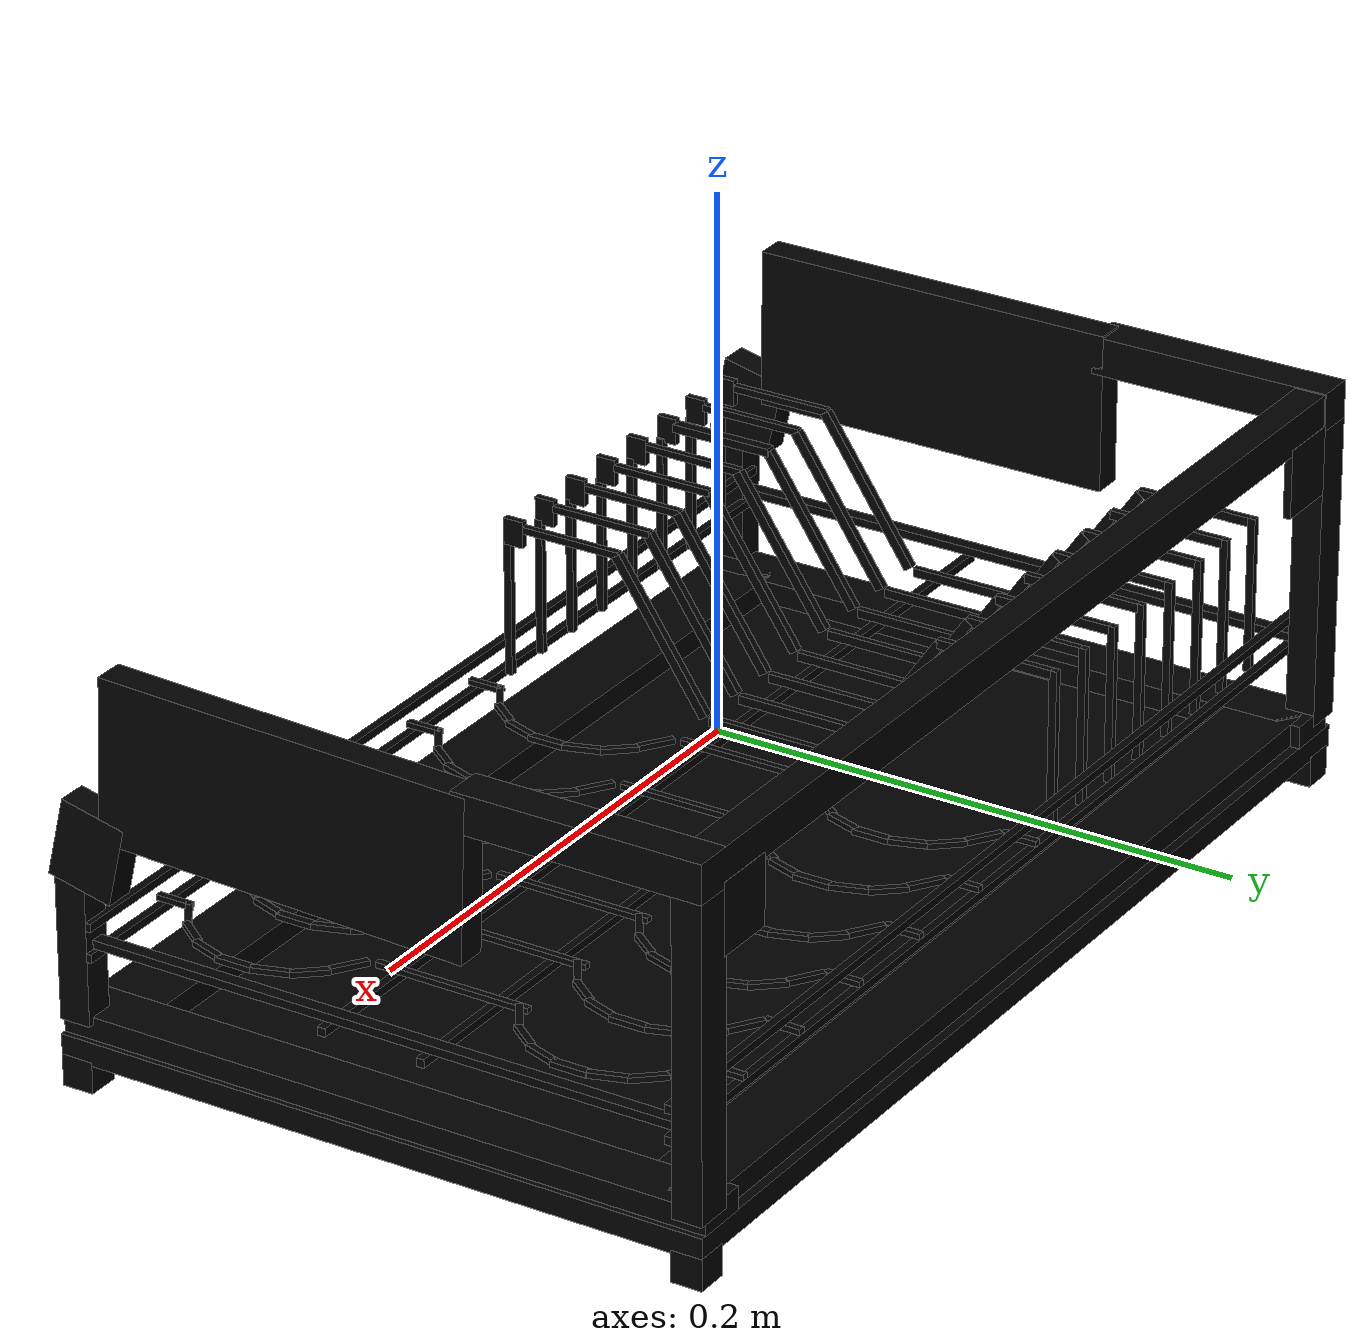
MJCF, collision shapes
<mujoco model="model">
  <option timestep="0.002" gravity="0.0 0.0 -9.81" />
  <compiler angle="radian" />
  <asset>
    <mesh file="visual/DishRack041.obj" name="DishRack041_vis" />
    <texture file="visual/T_BC001.png" name="DishRack041_material" type="2d" />
    <material name="DishRack041_material" rgba="1 1 1 1.0" texture="DishRack041_material" shininess="0.4472135901451111" specular="0.3103448502657381" />
  </asset>
  <default>
    <default class="visual">
      <geom conaffinity="0" contype="0" group="2" type="mesh" density="0" />
    </default>
    <default class="collision">
      <geom group="3" rgba="1 1 1 0.25" density="0" solref="0.004 1" solimp="0.998 0.998 0.001" friction="0.5" />
    </default>
    <default class="spawn">
      <geom group="0" rgba="1 1 1 0.5" contype="0" conaffinity="0" />
      <site group="0" rgba="1 1 1 0.5" />
    </default>
    <default class="region">
      <geom group="1" conaffinity="0" contype="0" rgba="0 1 0 0" mass="0" />
    </default>
  </default>
  <worldbody>
    <body>
      <body name="object">
        <geom mesh="DishRack041_vis" type="mesh" class="visual" material="DishRack041_material" group="2" contype="0" conaffinity="0" density="0" mass="0.5" />
        <geom type="box" pos="-0.20499955 -0.11976144 -0.06902253" size="0.006034868769347668 0.006034720689058304 0.005978831555694342" quat="1.0 0.0 0.0 0.0" class="collision" group="3" rgba="0 0 0 0" density="0" friction="0.5" solref="0.004 1" solimp="0.998 0.998 0.001" />
        <geom type="box" pos="-0.20499955 0.11968233 -0.06902253" size="0.006034869235008955 0.006034721154719591 0.005978832021355629" quat="1.0 0.0 0.0 0.0" class="collision" group="3" rgba="0 0 0 0" density="0" friction="0.5" solref="0.004 1" solimp="0.998 0.998 0.001" />
        <geom type="box" pos="0.20498709 0.11968233 -0.06902253" size="0.00603487016633153 0.006034722086042166 0.005978832487016916" quat="1.0 0.0 0.0 0.0" class="collision" group="3" rgba="0 0 0 0" density="0" friction="0.5" solref="0.004 1" solimp="0.998 0.998 0.001" />
        <geom type="box" pos="0.20498709 -0.11977387 -0.06902253" size="0.006034871097654104 0.006034722551703453 0.005978832487016916" quat="1.0 0.0 0.0 0.0" class="collision" group="3" rgba="0 0 0 0" density="0" friction="0.5" solref="0.004 1" solimp="0.998 0.998 0.001" />
        <geom type="box" pos="-0.00061250 -0.00006126 -0.05979588" size="0.21163222193717957 0.12574626505374908 0.004442216828465462" quat="1.0 0.0 0.0 0.0" class="collision" group="3" rgba="0 0 0 0" density="0" friction="0.5" solref="0.004 1" solimp="0.998 0.998 0.001" />
        <geom type="box" pos="0.20537086 -0.03480111 0.05003294" size="0.0056511941365897655 0.0711166188120842 0.030421923846006393" quat="0.9998422265052795 -0.01776234805583954 -0.0 0.0" class="collision" group="3" rgba="0 0 0 0" density="0" friction="0.5" solref="0.004 1" solimp="0.998 0.998 0.001" />
        <geom type="box" pos="0.20537086 -0.11268605 0.01644948" size="0.0056511941365897655 0.012520523741841316 0.015021923929452896" quat="0.9937589168548584 -0.11154916882514954 -0.0 0.0" class="collision" group="3" rgba="0 0 0 0" density="0" friction="0.5" solref="0.004 1" solimp="0.998 0.998 0.001" />
        <geom type="box" pos="0.20537086 -0.11988796 -0.02049373" size="0.00565115874633193 0.005920676048845053 0.02907174825668335" quat="1.0 0.0 0.0 0.0" class="collision" group="3" rgba="0 0 0 0" density="0" friction="0.5" solref="0.004 1" solimp="0.998 0.998 0.001" />
        <geom type="box" pos="0.20371896 0.12001329 0.00672089" size="0.007303008809685707 0.005672820843756199 0.05813051015138626" quat="1.0 0.0 0.0 0.0" class="collision" group="3" rgba="0 0 0 0" density="0" friction="0.5" solref="0.004 1" solimp="0.998 0.998 0.001" />
        <geom type="box" pos="0.00590863 0.11987413 0.07204802" size="0.20511117577552795 0.0058119758032262325 0.007242751773446798" quat="1.0 0.0 0.0 0.0" class="collision" group="3" rgba="0 0 0 0" density="0" friction="0.5" solref="0.004 1" solimp="0.998 0.998 0.001" />
        <geom type="box" pos="0.20371896 0.07880966 0.07204802" size="0.007303010206669569 0.046876210719347 0.00724275317043066" quat="1.0 0.0 0.0 0.0" class="collision" group="3" rgba="0 0 0 0" density="0" friction="0.5" solref="0.004 1" solimp="0.998 0.998 0.001" />
        <geom type="box" pos="-0.20725405 0.07880966 0.07204802" size="0.007303011137992144 0.0468762144446373 0.00724275317043066" quat="1.0 0.0 0.0 0.0" class="collision" group="3" rgba="0 0 0 0" density="0" friction="0.5" solref="0.004 1" solimp="0.998 0.998 0.001" />
        <geom type="box" pos="-0.20725405 0.12001329 0.00672089" size="0.007303011603653431 0.005672822240740061 0.05813053250312805" quat="1.0 0.0 0.0 0.0" class="collision" group="3" rgba="0 0 0 0" density="0" friction="0.5" solref="0.004 1" solimp="0.998 0.998 0.001" />
        <geom type="box" pos="-0.20560215 -0.11268605 0.01644948" size="0.0056511941365897655 0.012520523741841316 0.015021923929452896" quat="0.9937589168548584 -0.11154916882514954 -0.0 0.0" class="collision" group="3" rgba="0 0 0 0" density="0" friction="0.5" solref="0.004 1" solimp="0.998 0.998 0.001" />
        <geom type="box" pos="-0.20560215 -0.11988796 -0.02049373" size="0.005651161074638367 0.005920678377151489 0.029071766883134842" quat="1.0 0.0 0.0 0.0" class="collision" group="3" rgba="0 0 0 0" density="0" friction="0.5" solref="0.004 1" solimp="0.998 0.998 0.001" />
        <geom type="box" pos="-0.20560215 -0.03480111 0.04964730" size="0.005651161074638367 0.07111608982086182 0.030421655625104904" quat="1.0 0.0 0.0 0.0" class="collision" group="3" rgba="0 0 0 0" density="0" friction="0.5" solref="0.004 1" solimp="0.998 0.998 0.001" />
        <geom type="box" pos="0.00227845 -0.11360306 -0.02329872" size="0.20874150097370148 0.0015127251390367746 0.0015663657104596496" quat="1.0 0.0 0.0 0.0" class="collision" group="3" rgba="0 0 0 0" density="0" friction="0.5" solref="0.004 1" solimp="0.998 0.998 0.001" />
        <geom type="box" pos="0.00227845 -0.11360306 -0.01176763" size="0.20874153077602386 0.0015127252554520965 0.0015663658268749714" quat="1.0 0.0 0.0 0.0" class="collision" group="3" rgba="0 0 0 0" density="0" friction="0.5" solref="0.004 1" solimp="0.998 0.998 0.001" />
        <geom type="box" pos="0.00227845 0.11306563 -0.01176763" size="0.20874154567718506 0.0015127254882827401 0.001566366059705615" quat="1.0 0.0 0.0 0.0" class="collision" group="3" rgba="0 0 0 0" density="0" friction="0.5" solref="0.004 1" solimp="0.998 0.998 0.001" />
        <geom type="box" pos="0.00227845 0.11306563 -0.02329872" size="0.20874157547950745 0.001512725604698062 0.0015663661761209369" quat="1.0 0.0 0.0 0.0" class="collision" group="3" rgba="0 0 0 0" density="0" friction="0.5" solref="0.004 1" solimp="0.998 0.998 0.001" />
        <geom type="box" pos="0.00227845 0.01854266 -0.02329872" size="0.20874159038066864 0.0015127258375287056 0.0015663664089515805" quat="1.0 0.0 0.0 0.0" class="collision" group="3" rgba="0 0 0 0" density="0" friction="0.5" solref="0.004 1" solimp="0.998 0.998 0.001" />
        <geom type="box" pos="0.00227845 -0.02001187 -0.02329872" size="0.20874162018299103 0.0015127259539440274 0.0015663665253669024" quat="1.0 0.0 0.0 0.0" class="collision" group="3" rgba="0 0 0 0" density="0" friction="0.5" solref="0.004 1" solimp="0.998 0.998 0.001" />
        <geom type="box" pos="0.20483638 -0.00016860 -0.01980462" size="0.002513597020879388 0.11543918401002884 0.001566366758197546" quat="1.0 0.0 0.0 0.0" class="collision" group="3" rgba="0 0 0 0" density="0" friction="0.5" solref="0.004 1" solimp="0.998 0.998 0.001" />
        <geom type="box" pos="-0.20515107 -0.00016860 -0.01980462" size="0.0025135972537100315 0.11543919146060944 0.0015663668746128678" quat="1.0 0.0 0.0 0.0" class="collision" group="3" rgba="0 0 0 0" density="0" friction="0.5" solref="0.004 1" solimp="0.998 0.998 0.001" />
        <geom type="box" pos="-0.02073891 0.00228115 -0.02033602" size="0.0012615813175216317 0.029907487332820892 0.0010349740041419864" quat="1.0 0.0 0.0 0.0" class="collision" group="3" rgba="0 0 0 0" density="0" friction="0.5" solref="0.004 1" solimp="0.998 0.998 0.001" />
        <geom type="box" pos="-0.03891834 -0.11081605 0.00232781" size="0.0012615812011063099 0.0014540024567395449 0.026241205632686615" quat="1.0 0.0 0.0 0.0" class="collision" group="3" rgba="0 0 0 0" density="0" friction="0.5" solref="0.004 1" solimp="0.998 0.998 0.001" />
        <geom type="box" pos="-0.03891834 -0.10821144 0.03224378" size="0.0012615813175216317 0.003888410050421953 0.005072547122836113" quat="1.0 0.0 0.0 0.0" class="collision" group="3" rgba="0 0 0 0" density="0" friction="0.5" solref="0.004 1" solimp="0.998 0.998 0.001" />
        <geom type="box" pos="-0.03891834 -0.08481420 0.03431441" size="0.0012615814339369535 0.02004888467490673 0.0013131308369338512" quat="1.0 0.0 0.0 0.0" class="collision" group="3" rgba="0 0 0 0" density="0" friction="0.5" solref="0.004 1" solimp="0.998 0.998 0.001" />
        <geom type="box" pos="-0.03891834 0.00069457 -0.02016848" size="0.0012615815503522754 0.028269343078136444 0.0016950407298281789" quat="1.0 0.0 0.0 0.0" class="collision" group="3" rgba="0 0 0 0" density="0" friction="0.5" solref="0.004 1" solimp="0.998 0.998 0.001" />
        <geom type="box" pos="-0.03891834 0.10960148 0.00614335" size="0.0012615815503522754 0.001444814377464354 0.029950587078928947" quat="1.0 0.0 0.0 0.0" class="collision" group="3" rgba="0 0 0 0" density="0" friction="0.5" solref="0.004 1" solimp="0.998 0.998 0.001" />
        <geom type="box" pos="-0.03891834 0.04678638 0.00746748" size="0.0012615886516869068 0.03220853954553604 0.0018466416513547301" quat="0.8832719922065735 0.468860924243927 0.0 0.0" class="collision" group="3" rgba="0 0 0 0" density="0" friction="0.5" solref="0.004 1" solimp="0.998 0.998 0.001" />
        <geom type="box" pos="-0.03891834 0.08640634 0.03439917" size="0.0012615816667675972 0.022330930456519127 0.0016949691344052553" quat="1.0 0.0 0.0 0.0" class="collision" group="3" rgba="0 0 0 0" density="0" friction="0.5" solref="0.004 1" solimp="0.998 0.998 0.001" />
        <geom type="box" pos="-0.05897414 0.08640634 0.03439917" size="0.001261581783182919 0.022330930456519127 0.0016949691344052553" quat="1.0 0.0 0.0 0.0" class="collision" group="3" rgba="0 0 0 0" density="0" friction="0.5" solref="0.004 1" solimp="0.998 0.998 0.001" />
        <geom type="box" pos="-0.05897414 0.04678638 0.00746748" size="0.0012615886516869068 0.03220853954553604 0.0018466416513547301" quat="0.8832719922065735 0.468860924243927 0.0 0.0" class="collision" group="3" rgba="0 0 0 0" density="0" friction="0.5" solref="0.004 1" solimp="0.998 0.998 0.001" />
        <geom type="box" pos="-0.05897414 0.10960148 0.00614335" size="0.0012615818995982409 0.0014448147267103195 0.029950596392154694" quat="1.0 0.0 0.0 0.0" class="collision" group="3" rgba="0 0 0 0" density="0" friction="0.5" solref="0.004 1" solimp="0.998 0.998 0.001" />
        <geom type="box" pos="-0.05897414 0.00069457 -0.02016848" size="0.0012615820160135627 0.02826935611665249 0.0016950415447354317" quat="1.0 0.0 0.0 0.0" class="collision" group="3" rgba="0 0 0 0" density="0" friction="0.5" solref="0.004 1" solimp="0.998 0.998 0.001" />
        <geom type="box" pos="-0.05897414 -0.08481420 0.03431441" size="0.0012615820160135627 0.020048895850777626 0.0013131314190104604" quat="1.0 0.0 0.0 0.0" class="collision" group="3" rgba="0 0 0 0" density="0" friction="0.5" solref="0.004 1" solimp="0.998 0.998 0.001" />
        <geom type="box" pos="-0.05897414 -0.10821144 0.03224378" size="0.0012615821324288845 0.003888412844389677 0.005072550382465124" quat="1.0 0.0 0.0 0.0" class="collision" group="3" rgba="0 0 0 0" density="0" friction="0.5" solref="0.004 1" solimp="0.998 0.998 0.001" />
        <geom type="box" pos="-0.05897414 -0.11081605 0.00232781" size="0.0012615822488442063 0.0014540036208927631 0.026241237297654152" quat="1.0 0.0 0.0 0.0" class="collision" group="3" rgba="0 0 0 0" density="0" friction="0.5" solref="0.004 1" solimp="0.998 0.998 0.001" />
        <geom type="box" pos="-0.07884455 -0.11081605 0.00232781" size="0.0012615823652595282 0.0014540036208927631 0.0262412391602993" quat="1.0 0.0 0.0 0.0" class="collision" group="3" rgba="0 0 0 0" density="0" friction="0.5" solref="0.004 1" solimp="0.998 0.998 0.001" />
        <geom type="box" pos="-0.07884455 -0.10821144 0.03224378" size="0.0012615823652595282 0.003888414241373539 0.005072551313787699" quat="1.0 0.0 0.0 0.0" class="collision" group="3" rgba="0 0 0 0" density="0" friction="0.5" solref="0.004 1" solimp="0.998 0.998 0.001" />
        <geom type="box" pos="-0.07884455 -0.08481420 0.03431441" size="0.00126158248167485 0.020048901438713074 0.0013131318846717477" quat="1.0 0.0 0.0 0.0" class="collision" group="3" rgba="0 0 0 0" density="0" friction="0.5" solref="0.004 1" solimp="0.998 0.998 0.001" />
        <geom type="box" pos="-0.07884455 0.00069457 -0.02016848" size="0.0012615825980901718 0.02826937846839428 0.0016950428253039718" quat="1.0 0.0 0.0 0.0" class="collision" group="3" rgba="0 0 0 0" density="0" friction="0.5" solref="0.004 1" solimp="0.998 0.998 0.001" />
        <geom type="box" pos="-0.07884455 0.10960148 0.00614335" size="0.0012615827145054936 0.0014448155416175723 0.029950622469186783" quat="1.0 0.0 0.0 0.0" class="collision" group="3" rgba="0 0 0 0" density="0" friction="0.5" solref="0.004 1" solimp="0.998 0.998 0.001" />
        <geom type="box" pos="-0.07884455 0.04678638 0.00746748" size="0.0012615886516869068 0.03220853954553604 0.0018466416513547301" quat="0.8832719922065735 0.468860924243927 0.0 0.0" class="collision" group="3" rgba="0 0 0 0" density="0" friction="0.5" solref="0.004 1" solimp="0.998 0.998 0.001" />
        <geom type="box" pos="-0.07884455 0.08640634 0.03439917" size="0.0012615827145054936 0.02233094722032547 0.0016949712298810482" quat="1.0 0.0 0.0 0.0" class="collision" group="3" rgba="0 0 0 0" density="0" friction="0.5" solref="0.004 1" solimp="0.998 0.998 0.001" />
        <geom type="box" pos="-0.09878767 0.08640634 0.03439917" size="0.0012615828309208155 0.02233094722032547 0.0016949712298810482" quat="1.0 0.0 0.0 0.0" class="collision" group="3" rgba="0 0 0 0" density="0" friction="0.5" solref="0.004 1" solimp="0.998 0.998 0.001" />
        <geom type="box" pos="-0.09878767 0.04678638 0.00746748" size="0.0012615886516869068 0.03220853954553604 0.0018466416513547301" quat="0.8832719922065735 0.468860924243927 0.0 0.0" class="collision" group="3" rgba="0 0 0 0" density="0" friction="0.5" solref="0.004 1" solimp="0.998 0.998 0.001" />
        <geom type="box" pos="-0.09878767 0.10960148 0.00614335" size="0.0012615829473361373 0.001444815774448216 0.02995062991976738" quat="1.0 0.0 0.0 0.0" class="collision" group="3" rgba="0 0 0 0" density="0" friction="0.5" solref="0.004 1" solimp="0.998 0.998 0.001" />
        <geom type="box" pos="-0.09878767 0.00069457 -0.02016848" size="0.0012615830637514591 0.028269389644265175 0.0016950437566265464" quat="1.0 0.0 0.0 0.0" class="collision" group="3" rgba="0 0 0 0" density="0" friction="0.5" solref="0.004 1" solimp="0.998 0.998 0.001" />
        <geom type="box" pos="-0.09878767 -0.08481420 0.03431441" size="0.0012615830637514591 0.02004891261458397 0.0013131325831636786" quat="1.0 0.0 0.0 0.0" class="collision" group="3" rgba="0 0 0 0" density="0" friction="0.5" solref="0.004 1" solimp="0.998 0.998 0.001" />
        <geom type="box" pos="-0.09878767 -0.10821144 0.03224378" size="0.001261583180166781 0.003888417035341263 0.00507255457341671" quat="1.0 0.0 0.0 0.0" class="collision" group="3" rgba="0 0 0 0" density="0" friction="0.5" solref="0.004 1" solimp="0.998 0.998 0.001" />
        <geom type="box" pos="-0.09878767 -0.11081605 0.00232781" size="0.0012615832965821028 0.0014540046686306596 0.026241270825266838" quat="1.0 0.0 0.0 0.0" class="collision" group="3" rgba="0 0 0 0" density="0" friction="0.5" solref="0.004 1" solimp="0.998 0.998 0.001" />
        <geom type="box" pos="-0.11914092 -0.11081605 0.00232781" size="0.0012615834129974246 0.0014540046686306596 0.026241272687911987" quat="1.0 0.0 0.0 0.0" class="collision" group="3" rgba="0 0 0 0" density="0" friction="0.5" solref="0.004 1" solimp="0.998 0.998 0.001" />
        <geom type="box" pos="-0.11914092 -0.10821144 0.03224378" size="0.0012615835294127464 0.0038884186651557684 0.0050725555047392845" quat="1.0 0.0 0.0 0.0" class="collision" group="3" rgba="0 0 0 0" density="0" friction="0.5" solref="0.004 1" solimp="0.998 0.998 0.001" />
        <geom type="box" pos="-0.11914092 -0.08481420 0.03431441" size="0.0012615835294127464 0.020048920065164566 0.0013131329324096441" quat="1.0 0.0 0.0 0.0" class="collision" group="3" rgba="0 0 0 0" density="0" friction="0.5" solref="0.004 1" solimp="0.998 0.998 0.001" />
        <geom type="box" pos="-0.11914092 0.00069457 -0.02016848" size="0.0012615836458280683 0.028269411996006966 0.0016950450371950865" quat="1.0 0.0 0.0 0.0" class="collision" group="3" rgba="0 0 0 0" density="0" friction="0.5" solref="0.004 1" solimp="0.998 0.998 0.001" />
        <geom type="box" pos="-0.11914092 0.10960148 0.00614335" size="0.00126158376224339 0.0014448165893554688 0.02995065599679947" quat="1.0 0.0 0.0 0.0" class="collision" group="3" rgba="0 0 0 0" density="0" friction="0.5" solref="0.004 1" solimp="0.998 0.998 0.001" />
        <geom type="box" pos="-0.11914092 0.04678638 0.00746748" size="0.0012615886516869068 0.03220853954553604 0.0018466416513547301" quat="0.8832719922065735 0.468860924243927 0.0 0.0" class="collision" group="3" rgba="0 0 0 0" density="0" friction="0.5" solref="0.004 1" solimp="0.998 0.998 0.001" />
        <geom type="box" pos="-0.11914092 0.08640634 0.03439917" size="0.001261583878658712 0.022330963984131813 0.001694973325356841" quat="1.0 0.0 0.0 0.0" class="collision" group="3" rgba="0 0 0 0" density="0" friction="0.5" solref="0.004 1" solimp="0.998 0.998 0.001" />
        <geom type="box" pos="-0.13966642 0.08640634 0.03439917" size="0.001261583878658712 0.022330963984131813 0.001694973325356841" quat="1.0 0.0 0.0 0.0" class="collision" group="3" rgba="0 0 0 0" density="0" friction="0.5" solref="0.004 1" solimp="0.998 0.998 0.001" />
        <geom type="box" pos="-0.13966642 0.04678638 0.00746748" size="0.0012615886516869068 0.03220853954553604 0.0018466416513547301" quat="0.8832719922065735 0.468860924243927 0.0 0.0" class="collision" group="3" rgba="0 0 0 0" density="0" friction="0.5" solref="0.004 1" solimp="0.998 0.998 0.001" />
        <geom type="box" pos="-0.13966642 0.10960148 0.00614335" size="0.0012615839950740337 0.0014448168221861124 0.029950665310025215" quat="1.0 0.0 0.0 0.0" class="collision" group="3" rgba="0 0 0 0" density="0" friction="0.5" solref="0.004 1" solimp="0.998 0.998 0.001" />
        <geom type="box" pos="-0.13966642 0.00069457 -0.02016848" size="0.0012615841114893556 0.02826942317187786 0.0016950458521023393" quat="1.0 0.0 0.0 0.0" class="collision" group="3" rgba="0 0 0 0" density="0" friction="0.5" solref="0.004 1" solimp="0.998 0.998 0.001" />
        <geom type="box" pos="-0.13929930 -0.08481420 0.03431441" size="0.0020217648707330227 0.020048929378390312 0.0015507052885368466" quat="1.0 0.0 0.0 0.0" class="collision" group="3" rgba="0 0 0 0" density="0" friction="0.5" solref="0.004 1" solimp="0.998 0.998 0.001" />
        <geom type="box" pos="-0.13966642 -0.10821144 0.03224378" size="0.0012615842279046774 0.0038884214591234922 0.005072558764368296" quat="1.0 0.0 0.0 0.0" class="collision" group="3" rgba="0 0 0 0" density="0" friction="0.5" solref="0.004 1" solimp="0.998 0.998 0.001" />
        <geom type="box" pos="-0.13920130 -0.11081605 0.00232781" size="0.0015401322161778808 0.0014540100237354636 0.026241442188620567" quat="1.0 0.0 0.0 0.0" class="collision" group="3" rgba="0 0 0 0" density="0" friction="0.5" solref="0.004 1" solimp="0.998 0.998 0.001" />
        <geom type="box" pos="-0.15891659 -0.11081605 0.00232781" size="0.001261584460735321 0.001454005716368556 0.026241308078169823" quat="1.0 0.0 0.0 0.0" class="collision" group="3" rgba="0 0 0 0" density="0" friction="0.5" solref="0.004 1" solimp="0.998 0.998 0.001" />
        <geom type="box" pos="-0.15891659 -0.10821144 0.03224378" size="0.0012615845771506429 0.003888422856107354 0.00507255969569087" quat="1.0 0.0 0.0 0.0" class="collision" group="3" rgba="0 0 0 0" density="0" friction="0.5" solref="0.004 1" solimp="0.998 0.998 0.001" />
        <geom type="box" pos="-0.15891659 -0.08481420 0.03431441" size="0.0012615846935659647 0.02004893682897091 0.0013131340965628624" quat="1.0 0.0 0.0 0.0" class="collision" group="3" rgba="0 0 0 0" density="0" friction="0.5" solref="0.004 1" solimp="0.998 0.998 0.001" />
        <geom type="box" pos="-0.15891659 0.00069457 -0.02016848" size="0.0012615846935659647 0.0282694473862648 0.0016950471326708794" quat="1.0 0.0 0.0 0.0" class="collision" group="3" rgba="0 0 0 0" density="0" friction="0.5" solref="0.004 1" solimp="0.998 0.998 0.001" />
        <geom type="box" pos="-0.15891659 0.10960148 0.00614335" size="0.0012615848099812865 0.0014448176370933652 0.029950689524412155" quat="1.0 0.0 0.0 0.0" class="collision" group="3" rgba="0 0 0 0" density="0" friction="0.5" solref="0.004 1" solimp="0.998 0.998 0.001" />
        <geom type="box" pos="-0.15891659 0.04678638 0.00746748" size="0.0012615886516869068 0.03220853954553604 0.0018466416513547301" quat="0.8832719922065735 0.468860924243927 0.0 0.0" class="collision" group="3" rgba="0 0 0 0" density="0" friction="0.5" solref="0.004 1" solimp="0.998 0.998 0.001" />
        <geom type="box" pos="-0.15891659 0.08640634 0.03439917" size="0.0012615849263966084 0.022330982610583305 0.0016949755372479558" quat="1.0 0.0 0.0 0.0" class="collision" group="3" rgba="0 0 0 0" density="0" friction="0.5" solref="0.004 1" solimp="0.998 0.998 0.001" />
        <geom type="box" pos="-0.17906566 0.08640634 0.03439917" size="0.0012615850428119302 0.022330982610583305 0.0016949755372479558" quat="1.0 0.0 0.0 0.0" class="collision" group="3" rgba="0 0 0 0" density="0" friction="0.5" solref="0.004 1" solimp="0.998 0.998 0.001" />
        <geom type="box" pos="-0.17906566 0.04678638 0.00746748" size="0.0012615886516869068 0.03220853954553604 0.0018466416513547301" quat="0.8832719922065735 0.468860924243927 0.0 0.0" class="collision" group="3" rgba="0 0 0 0" density="0" friction="0.5" solref="0.004 1" solimp="0.998 0.998 0.001" />
        <geom type="box" pos="-0.17906566 0.10960148 0.00614335" size="0.0012615850428119302 0.0014448178699240088 0.0299506988376379" quat="1.0 0.0 0.0 0.0" class="collision" group="3" rgba="0 0 0 0" density="0" friction="0.5" solref="0.004 1" solimp="0.998 0.998 0.001" />
        <geom type="box" pos="-0.17906566 0.00069457 -0.02016848" size="0.001261585159227252 0.028269458562135696 0.001695048063993454" quat="1.0 0.0 0.0 0.0" class="collision" group="3" rgba="0 0 0 0" density="0" friction="0.5" solref="0.004 1" solimp="0.998 0.998 0.001" />
        <geom type="box" pos="-0.17906566 -0.08481420 0.03431441" size="0.0012615852756425738 0.020048946142196655 0.0013131346786394715" quat="1.0 0.0 0.0 0.0" class="collision" group="3" rgba="0 0 0 0" density="0" friction="0.5" solref="0.004 1" solimp="0.998 0.998 0.001" />
        <geom type="box" pos="-0.17906566 -0.10821144 0.03224378" size="0.0012615853920578957 0.003888425650075078 0.0050725629553198814" quat="1.0 0.0 0.0 0.0" class="collision" group="3" rgba="0 0 0 0" density="0" friction="0.5" solref="0.004 1" solimp="0.998 0.998 0.001" />
        <geom type="box" pos="-0.17906566 -0.11081605 0.00232781" size="0.0012615853920578957 0.0014540067641064525 0.02624133974313736" quat="1.0 0.0 0.0 0.0" class="collision" group="3" rgba="0 0 0 0" density="0" friction="0.5" solref="0.004 1" solimp="0.998 0.998 0.001" />
        <geom type="box" pos="-0.18805820 0.12436122 0.05383100" size="0.01203637570142746 0.001444816356524825 0.013210675679147243" quat="1.0 0.0 0.0 0.0" class="collision" group="3" rgba="0 0 0 0" density="0" friction="0.5" solref="0.004 1" solimp="0.998 0.998 0.001" />
        <geom type="box" pos="0.18571559 0.12436122 0.05383100" size="0.012036377564072609 0.001444816356524825 0.013210676610469818" quat="1.0 0.0 0.0 0.0" class="collision" group="3" rgba="0 0 0 0" density="0" friction="0.5" solref="0.004 1" solimp="0.998 0.998 0.001" />
        <geom type="box" pos="0.01805753 0.00228115 -0.02033602" size="0.001261585857719183 0.029907632619142532 0.0010349785443395376" quat="1.0 0.0 0.0 0.0" class="collision" group="3" rgba="0 0 0 0" density="0" friction="0.5" solref="0.004 1" solimp="0.998 0.998 0.001" />
        <geom type="box" pos="0.05662841 0.00228115 -0.02033602" size="0.0012615859741345048 0.02990763448178768 0.0010349786607548594" quat="1.0 0.0 0.0 0.0" class="collision" group="3" rgba="0 0 0 0" density="0" friction="0.5" solref="0.004 1" solimp="0.998 0.998 0.001" />
        <geom type="box" pos="0.09489894 0.00228115 -0.02033602" size="0.0012615860905498266 0.02990763820707798 0.0010349787771701813" quat="1.0 0.0 0.0 0.0" class="collision" group="3" rgba="0 0 0 0" density="0" friction="0.5" solref="0.004 1" solimp="0.998 0.998 0.001" />
        <geom type="box" pos="0.13268788 0.00228115 -0.02033602" size="0.0012615862069651484 0.02990764193236828 0.0010349787771701813" quat="1.0 0.0 0.0 0.0" class="collision" group="3" rgba="0 0 0 0" density="0" friction="0.5" solref="0.004 1" solimp="0.998 0.998 0.001" />
        <geom type="box" pos="0.16748273 0.00228115 -0.02033602" size="0.0012615862069651484 0.029907643795013428 0.001034978893585503" quat="1.0 0.0 0.0 0.0" class="collision" group="3" rgba="0 0 0 0" density="0" friction="0.5" solref="0.004 1" solimp="0.998 0.998 0.001" />
        <geom type="box" pos="0.19888650 -0.00006126 -0.05120076" size="0.009982718154788017 0.12574708461761475 0.004442242905497551" quat="1.0 0.0 0.0 0.0" class="collision" group="3" rgba="0 0 0 0" density="0" friction="0.5" solref="0.004 1" solimp="0.998 0.998 0.001" />
        <geom type="box" pos="-0.19941530 -0.00006126 -0.05120076" size="0.009982718154788017 0.12574709951877594 0.004442243371158838" quat="1.0 0.0 0.0 0.0" class="collision" group="3" rgba="0 0 0 0" density="0" friction="0.5" solref="0.004 1" solimp="0.998 0.998 0.001" />
        <geom type="box" pos="0.00057763 -0.11186486 -0.05120076" size="0.20226937532424927 0.013433815911412239 0.004442253150045872" quat="1.0 0.0 0.0 0.0" class="collision" group="3" rgba="0 0 0 0" density="0" friction="0.5" solref="0.004 1" solimp="0.998 0.998 0.001" />
        <geom type="box" pos="0.00057763 0.10864222 -0.05120076" size="0.20226937532424927 0.013433815911412239 0.004442253150045872" quat="1.0 0.0 0.0 0.0" class="collision" group="3" rgba="0 0 0 0" density="0" friction="0.5" solref="0.004 1" solimp="0.998 0.998 0.001" />
        <geom type="box" pos="-0.03891834 -0.04750177 0.00746748" size="0.0014921032125130296 0.03220853954553604 0.0018466416513547301" quat="6.668518182095795e-08 3.5398013409349005e-08 -0.468860924243927 -0.8832719922065735" class="collision" group="3" rgba="0 0 0 0" density="0" friction="0.5" solref="0.004 1" solimp="0.998 0.998 0.001" />
        <geom type="box" pos="-0.05932090 -0.04750177 0.00746748" size="0.0014921032125130296 0.03220853954553604 0.0018466416513547301" quat="6.668518182095795e-08 3.5398013409349005e-08 -0.468860924243927 -0.8832719922065735" class="collision" group="3" rgba="0 0 0 0" density="0" friction="0.5" solref="0.004 1" solimp="0.998 0.998 0.001" />
        <geom type="box" pos="-0.07883081 -0.04750177 0.00746748" size="0.0014921032125130296 0.03220853954553604 0.0018466416513547301" quat="6.668518182095795e-08 3.5398013409349005e-08 -0.468860924243927 -0.8832719922065735" class="collision" group="3" rgba="0 0 0 0" density="0" friction="0.5" solref="0.004 1" solimp="0.998 0.998 0.001" />
        <geom type="box" pos="-0.09920465 -0.04750177 0.00746748" size="0.0014921032125130296 0.03220853954553604 0.0018466416513547301" quat="6.668518182095795e-08 3.5398013409349005e-08 -0.468860924243927 -0.8832719922065735" class="collision" group="3" rgba="0 0 0 0" density="0" friction="0.5" solref="0.004 1" solimp="0.998 0.998 0.001" />
        <geom type="box" pos="-0.11884832 -0.04750177 0.00746748" size="0.0014921032125130296 0.03220853954553604 0.0018466416513547301" quat="6.668518182095795e-08 3.5398013409349005e-08 -0.468860924243927 -0.8832719922065735" class="collision" group="3" rgba="0 0 0 0" density="0" friction="0.5" solref="0.004 1" solimp="0.998 0.998 0.001" />
        <geom type="box" pos="-0.13938928 -0.04750177 0.00746748" size="0.0014921032125130296 0.03220853954553604 0.0018466416513547301" quat="6.668518182095795e-08 3.5398013409349005e-08 -0.468860924243927 -0.8832719922065735" class="collision" group="3" rgba="0 0 0 0" density="0" friction="0.5" solref="0.004 1" solimp="0.998 0.998 0.001" />
        <geom type="box" pos="-0.15863523 -0.04750177 0.00746748" size="0.0014921032125130296 0.03220853954553604 0.0018466416513547301" quat="6.668518182095795e-08 3.5398013409349005e-08 -0.468860924243927 -0.8832719922065735" class="collision" group="3" rgba="0 0 0 0" density="0" friction="0.5" solref="0.004 1" solimp="0.998 0.998 0.001" />
        <geom type="box" pos="-0.17877235 -0.04750177 0.00746748" size="0.0014921032125130296 0.03220853954553604 0.0018466416513547301" quat="6.668518182095795e-08 3.5398013409349005e-08 -0.468860924243927 -0.8832719922065735" class="collision" group="3" rgba="0 0 0 0" density="0" friction="0.5" solref="0.004 1" solimp="0.998 0.998 0.001" />
        <geom type="box" pos="-0.01366808 -0.03397605 -0.01999718" size="0.0012615887681022286 0.006920578423887491 0.0010349814547225833" quat="0.8809190988540649 0.0 0.0 0.47326692938804626" class="collision" group="3" rgba="0 0 0 0" density="0" friction="0.5" solref="0.004 1" solimp="0.998 0.998 0.001" />
        <geom type="box" pos="-0.00366493 -0.04256967 -0.02018545" size="0.0012615887681022286 0.006920579355210066 0.0010349814547225833" quat="0.9366821646690369 0.0 0.0 0.3501807451248169" class="collision" group="3" rgba="0 0 0 0" density="0" friction="0.5" solref="0.004 1" solimp="0.998 0.998 0.001" />
        <geom type="box" pos="0.00249082 -0.05419178 -0.02018545" size="0.0012615888845175505 0.006920578423887491 0.0010349814547225833" quat="0.9872344732284546 0.0 0.0 0.15927375853061676" class="collision" group="3" rgba="0 0 0 0" density="0" friction="0.5" solref="0.004 1" solimp="0.998 0.998 0.001" />
        <geom type="box" pos="0.00442649 -0.06726661 -0.02018545" size="0.0015448019839823246 0.006966559682041407 0.0010349814547225833" quat="1.0 0.0 0.0 0.0" class="collision" group="3" rgba="0 0 0 0" density="0" friction="0.5" solref="0.004 1" solimp="0.998 0.998 0.001" />
        <geom type="box" pos="0.00188024 -0.07985152 -0.02018545" size="0.0012615887681022286 0.006920578423887491 0.0010349814547225833" quat="0.9868403673171997 0.0 -0.0 -0.16169767081737518" class="collision" group="3" rgba="0 0 0 0" density="0" friction="0.5" solref="0.004 1" solimp="0.998 0.998 0.001" />
        <geom type="box" pos="-0.00507362 -0.09099808 -0.02018545" size="0.0012615887681022286 0.006920578423887491 0.0010349814547225833" quat="0.9477697014808655 0.0 -0.0 -0.31895554065704346" class="collision" group="3" rgba="0 0 0 0" density="0" friction="0.5" solref="0.004 1" solimp="0.998 0.998 0.001" />
        <geom type="box" pos="-0.01516932 -0.09969484 -0.02018545" size="0.0012615887681022286 0.006920579355210066 0.0010349814547225833" quat="0.8807778358459473 0.0 -0.0 -0.47352972626686096" class="collision" group="3" rgba="0 0 0 0" density="0" friction="0.5" solref="0.004 1" solimp="0.998 0.998 0.001" />
        <geom type="box" pos="-0.02038697 -0.10879981 -0.02018545" size="0.0013045015512034297 0.006928272545337677 0.0010349814547225833" quat="1.0 0.0 0.0 0.0" class="collision" group="3" rgba="0 0 0 0" density="0" friction="0.5" solref="0.004 1" solimp="0.998 0.998 0.001" />
        <geom type="box" pos="0.02502925 -0.03397605 -0.01999718" size="0.0012615887681022286 0.006920578423887491 0.0010349814547225833" quat="0.8809190988540649 0.0 0.0 0.47326692938804626" class="collision" group="3" rgba="0 0 0 0" density="0" friction="0.5" solref="0.004 1" solimp="0.998 0.998 0.001" />
        <geom type="box" pos="0.03503239 -0.04256967 -0.02018545" size="0.0012615887681022286 0.006920579355210066 0.0010349814547225833" quat="0.9366821646690369 0.0 0.0 0.3501807451248169" class="collision" group="3" rgba="0 0 0 0" density="0" friction="0.5" solref="0.004 1" solimp="0.998 0.998 0.001" />
        <geom type="box" pos="0.04118814 -0.05419178 -0.02018545" size="0.0012615888845175505 0.006920578423887491 0.0010349814547225833" quat="0.9872344732284546 0.0 0.0 0.15927375853061676" class="collision" group="3" rgba="0 0 0 0" density="0" friction="0.5" solref="0.004 1" solimp="0.998 0.998 0.001" />
        <geom type="box" pos="0.04312382 -0.06726661 -0.02018545" size="0.0015448019839823246 0.006966559682041407 0.0010349814547225833" quat="1.0 0.0 0.0 0.0" class="collision" group="3" rgba="0 0 0 0" density="0" friction="0.5" solref="0.004 1" solimp="0.998 0.998 0.001" />
        <geom type="box" pos="0.04057756 -0.07985152 -0.02018545" size="0.0012615887681022286 0.006920578423887491 0.0010349814547225833" quat="0.9868403673171997 0.0 -0.0 -0.16169767081737518" class="collision" group="3" rgba="0 0 0 0" density="0" friction="0.5" solref="0.004 1" solimp="0.998 0.998 0.001" />
        <geom type="box" pos="0.03362370 -0.09099808 -0.02018545" size="0.0012615887681022286 0.006920578423887491 0.0010349814547225833" quat="0.9477697014808655 0.0 -0.0 -0.31895554065704346" class="collision" group="3" rgba="0 0 0 0" density="0" friction="0.5" solref="0.004 1" solimp="0.998 0.998 0.001" />
        <geom type="box" pos="0.02352800 -0.09969484 -0.02018545" size="0.0012615887681022286 0.006920579355210066 0.0010349814547225833" quat="0.8807778358459473 0.0 -0.0 -0.47352972626686096" class="collision" group="3" rgba="0 0 0 0" density="0" friction="0.5" solref="0.004 1" solimp="0.998 0.998 0.001" />
        <geom type="box" pos="0.01831035 -0.10879981 -0.02018545" size="0.0013045015512034297 0.006928272545337677 0.0010349814547225833" quat="1.0 0.0 0.0 0.0" class="collision" group="3" rgba="0 0 0 0" density="0" friction="0.5" solref="0.004 1" solimp="0.998 0.998 0.001" />
        <geom type="box" pos="0.06387548 -0.03397605 -0.01999718" size="0.0012615887681022286 0.006920578423887491 0.0010349814547225833" quat="0.8809190988540649 0.0 0.0 0.47326692938804626" class="collision" group="3" rgba="0 0 0 0" density="0" friction="0.5" solref="0.004 1" solimp="0.998 0.998 0.001" />
        <geom type="box" pos="0.07387862 -0.04256967 -0.02018545" size="0.0012615887681022286 0.006920579355210066 0.0010349814547225833" quat="0.9366821646690369 0.0 0.0 0.3501807451248169" class="collision" group="3" rgba="0 0 0 0" density="0" friction="0.5" solref="0.004 1" solimp="0.998 0.998 0.001" />
        <geom type="box" pos="0.08003438 -0.05419178 -0.02018545" size="0.0012615888845175505 0.006920578423887491 0.0010349814547225833" quat="0.9872344732284546 0.0 0.0 0.15927375853061676" class="collision" group="3" rgba="0 0 0 0" density="0" friction="0.5" solref="0.004 1" solimp="0.998 0.998 0.001" />
        <geom type="box" pos="0.08197005 -0.06726661 -0.02018545" size="0.0015448019839823246 0.006966559682041407 0.0010349814547225833" quat="1.0 0.0 0.0 0.0" class="collision" group="3" rgba="0 0 0 0" density="0" friction="0.5" solref="0.004 1" solimp="0.998 0.998 0.001" />
        <geom type="box" pos="0.07942379 -0.07985152 -0.02018545" size="0.0012615887681022286 0.006920578423887491 0.0010349814547225833" quat="0.9868403673171997 0.0 -0.0 -0.16169767081737518" class="collision" group="3" rgba="0 0 0 0" density="0" friction="0.5" solref="0.004 1" solimp="0.998 0.998 0.001" />
        <geom type="box" pos="0.07246993 -0.09099808 -0.02018545" size="0.0012615887681022286 0.006920578423887491 0.0010349814547225833" quat="0.9477697014808655 0.0 -0.0 -0.31895554065704346" class="collision" group="3" rgba="0 0 0 0" density="0" friction="0.5" solref="0.004 1" solimp="0.998 0.998 0.001" />
        <geom type="box" pos="0.06237423 -0.09969484 -0.02018545" size="0.0012615887681022286 0.006920579355210066 0.0010349814547225833" quat="0.8807778358459473 0.0 -0.0 -0.47352972626686096" class="collision" group="3" rgba="0 0 0 0" density="0" friction="0.5" solref="0.004 1" solimp="0.998 0.998 0.001" />
        <geom type="box" pos="0.05715659 -0.10879981 -0.02018545" size="0.0013045015512034297 0.006928272545337677 0.0010349814547225833" quat="1.0 0.0 0.0 0.0" class="collision" group="3" rgba="0 0 0 0" density="0" friction="0.5" solref="0.004 1" solimp="0.998 0.998 0.001" />
        <geom type="box" pos="0.10242925 -0.03397605 -0.01999718" size="0.0012615887681022286 0.006920578423887491 0.0010349814547225833" quat="0.8809190988540649 0.0 0.0 0.47326692938804626" class="collision" group="3" rgba="0 0 0 0" density="0" friction="0.5" solref="0.004 1" solimp="0.998 0.998 0.001" />
        <geom type="box" pos="0.11243239 -0.04256967 -0.02018545" size="0.0012615887681022286 0.006920579355210066 0.0010349814547225833" quat="0.9366821646690369 0.0 0.0 0.3501807451248169" class="collision" group="3" rgba="0 0 0 0" density="0" friction="0.5" solref="0.004 1" solimp="0.998 0.998 0.001" />
        <geom type="box" pos="0.11858814 -0.05419178 -0.02018545" size="0.0012615888845175505 0.006920578423887491 0.0010349814547225833" quat="0.9872344732284546 0.0 0.0 0.15927375853061676" class="collision" group="3" rgba="0 0 0 0" density="0" friction="0.5" solref="0.004 1" solimp="0.998 0.998 0.001" />
        <geom type="box" pos="0.12052382 -0.06726661 -0.02018545" size="0.0015448019839823246 0.006966559682041407 0.0010349814547225833" quat="1.0 0.0 0.0 0.0" class="collision" group="3" rgba="0 0 0 0" density="0" friction="0.5" solref="0.004 1" solimp="0.998 0.998 0.001" />
        <geom type="box" pos="0.11797756 -0.07985152 -0.02018545" size="0.0012615887681022286 0.006920578423887491 0.0010349814547225833" quat="0.9868403673171997 0.0 -0.0 -0.16169767081737518" class="collision" group="3" rgba="0 0 0 0" density="0" friction="0.5" solref="0.004 1" solimp="0.998 0.998 0.001" />
        <geom type="box" pos="0.11102370 -0.09099808 -0.02018545" size="0.0012615887681022286 0.006920578423887491 0.0010349814547225833" quat="0.9477697014808655 0.0 -0.0 -0.31895554065704346" class="collision" group="3" rgba="0 0 0 0" density="0" friction="0.5" solref="0.004 1" solimp="0.998 0.998 0.001" />
        <geom type="box" pos="0.10092800 -0.09969484 -0.02018545" size="0.0012615887681022286 0.006920579355210066 0.0010349814547225833" quat="0.8807778358459473 0.0 -0.0 -0.47352972626686096" class="collision" group="3" rgba="0 0 0 0" density="0" friction="0.5" solref="0.004 1" solimp="0.998 0.998 0.001" />
        <geom type="box" pos="0.09571035 -0.10879981 -0.02018545" size="0.0013045015512034297 0.006928272545337677 0.0010349814547225833" quat="1.0 0.0 0.0 0.0" class="collision" group="3" rgba="0 0 0 0" density="0" friction="0.5" solref="0.004 1" solimp="0.998 0.998 0.001" />
        <geom type="box" pos="0.13934830 -0.03397605 -0.01999718" size="0.0012615887681022286 0.006920578423887491 0.0010349814547225833" quat="0.8809190988540649 0.0 0.0 0.47326692938804626" class="collision" group="3" rgba="0 0 0 0" density="0" friction="0.5" solref="0.004 1" solimp="0.998 0.998 0.001" />
        <geom type="box" pos="0.14935145 -0.04256967 -0.02018545" size="0.0012615887681022286 0.006920579355210066 0.0010349814547225833" quat="0.9366821646690369 0.0 0.0 0.3501807451248169" class="collision" group="3" rgba="0 0 0 0" density="0" friction="0.5" solref="0.004 1" solimp="0.998 0.998 0.001" />
        <geom type="box" pos="0.15550719 -0.05419178 -0.02018545" size="0.0012615888845175505 0.006920578423887491 0.0010349814547225833" quat="0.9872344732284546 0.0 0.0 0.15927375853061676" class="collision" group="3" rgba="0 0 0 0" density="0" friction="0.5" solref="0.004 1" solimp="0.998 0.998 0.001" />
        <geom type="box" pos="0.15744287 -0.06726661 -0.02018545" size="0.0015448019839823246 0.006966559682041407 0.0010349814547225833" quat="1.0 0.0 0.0 0.0" class="collision" group="3" rgba="0 0 0 0" density="0" friction="0.5" solref="0.004 1" solimp="0.998 0.998 0.001" />
        <geom type="box" pos="0.15489662 -0.07985152 -0.02018545" size="0.0012615887681022286 0.006920578423887491 0.0010349814547225833" quat="0.9868403673171997 0.0 -0.0 -0.16169767081737518" class="collision" group="3" rgba="0 0 0 0" density="0" friction="0.5" solref="0.004 1" solimp="0.998 0.998 0.001" />
        <geom type="box" pos="0.14794275 -0.09099808 -0.02018545" size="0.0012615887681022286 0.006920578423887491 0.0010349814547225833" quat="0.9477697014808655 0.0 -0.0 -0.31895554065704346" class="collision" group="3" rgba="0 0 0 0" density="0" friction="0.5" solref="0.004 1" solimp="0.998 0.998 0.001" />
        <geom type="box" pos="0.13784705 -0.09969484 -0.02018545" size="0.0012615887681022286 0.006920579355210066 0.0010349814547225833" quat="0.8807778358459473 0.0 -0.0 -0.47352972626686096" class="collision" group="3" rgba="0 0 0 0" density="0" friction="0.5" solref="0.004 1" solimp="0.998 0.998 0.001" />
        <geom type="box" pos="0.13262941 -0.10879981 -0.02018545" size="0.0013045015512034297 0.006928272545337677 0.0010349814547225833" quat="1.0 0.0 0.0 0.0" class="collision" group="3" rgba="0 0 0 0" density="0" friction="0.5" solref="0.004 1" solimp="0.998 0.998 0.001" />
        <geom type="box" pos="0.17448863 -0.03397605 -0.01999718" size="0.0012615887681022286 0.006920578423887491 0.0010349814547225833" quat="0.8809190988540649 0.0 0.0 0.47326692938804626" class="collision" group="3" rgba="0 0 0 0" density="0" friction="0.5" solref="0.004 1" solimp="0.998 0.998 0.001" />
        <geom type="box" pos="0.18449178 -0.04256967 -0.02018545" size="0.0012615887681022286 0.006920579355210066 0.0010349814547225833" quat="0.9366821646690369 0.0 0.0 0.3501807451248169" class="collision" group="3" rgba="0 0 0 0" density="0" friction="0.5" solref="0.004 1" solimp="0.998 0.998 0.001" />
        <geom type="box" pos="0.19064753 -0.05419178 -0.02018545" size="0.0012615888845175505 0.006920578423887491 0.0010349814547225833" quat="0.9872344732284546 0.0 0.0 0.15927375853061676" class="collision" group="3" rgba="0 0 0 0" density="0" friction="0.5" solref="0.004 1" solimp="0.998 0.998 0.001" />
        <geom type="box" pos="0.19258320 -0.06726661 -0.02018545" size="0.0015448019839823246 0.006966559682041407 0.0010349814547225833" quat="1.0 0.0 0.0 0.0" class="collision" group="3" rgba="0 0 0 0" density="0" friction="0.5" solref="0.004 1" solimp="0.998 0.998 0.001" />
        <geom type="box" pos="0.19003695 -0.07985152 -0.02018545" size="0.0012615887681022286 0.006920578423887491 0.0010349814547225833" quat="0.9868403673171997 0.0 -0.0 -0.16169767081737518" class="collision" group="3" rgba="0 0 0 0" density="0" friction="0.5" solref="0.004 1" solimp="0.998 0.998 0.001" />
        <geom type="box" pos="0.18308309 -0.09099808 -0.02018545" size="0.0012615887681022286 0.006920578423887491 0.0010349814547225833" quat="0.9477697014808655 0.0 -0.0 -0.31895554065704346" class="collision" group="3" rgba="0 0 0 0" density="0" friction="0.5" solref="0.004 1" solimp="0.998 0.998 0.001" />
        <geom type="box" pos="0.17298739 -0.09969484 -0.02018545" size="0.0012615887681022286 0.006920579355210066 0.0010349814547225833" quat="0.8807778358459473 0.0 -0.0 -0.47352972626686096" class="collision" group="3" rgba="0 0 0 0" density="0" friction="0.5" solref="0.004 1" solimp="0.998 0.998 0.001" />
        <geom type="box" pos="0.16776974 -0.10879981 -0.02018545" size="0.0013045015512034297 0.006928272545337677 0.0010349814547225833" quat="1.0 0.0 0.0 0.0" class="collision" group="3" rgba="0 0 0 0" density="0" friction="0.5" solref="0.004 1" solimp="0.998 0.998 0.001" />
        <geom type="box" pos="0.17448863 0.09753564 -0.01999718" size="0.0012615887681022286 0.006920578423887491 0.0010349814547225833" quat="0.8809190988540649 0.0 0.0 0.47326692938804626" class="collision" group="3" rgba="0 0 0 0" density="0" friction="0.5" solref="0.004 1" solimp="0.998 0.998 0.001" />
        <geom type="box" pos="0.18449178 0.08894201 -0.02018545" size="0.0012615887681022286 0.006920579355210066 0.0010349814547225833" quat="0.9366821646690369 0.0 0.0 0.3501807451248169" class="collision" group="3" rgba="0 0 0 0" density="0" friction="0.5" solref="0.004 1" solimp="0.998 0.998 0.001" />
        <geom type="box" pos="0.19064753 0.07731991 -0.02018545" size="0.0012615888845175505 0.006920578423887491 0.0010349814547225833" quat="0.9872344732284546 0.0 0.0 0.15927375853061676" class="collision" group="3" rgba="0 0 0 0" density="0" friction="0.5" solref="0.004 1" solimp="0.998 0.998 0.001" />
        <geom type="box" pos="0.19258320 0.06424508 -0.02018545" size="0.0015448019839823246 0.006966559682041407 0.0010349814547225833" quat="1.0 0.0 0.0 0.0" class="collision" group="3" rgba="0 0 0 0" density="0" friction="0.5" solref="0.004 1" solimp="0.998 0.998 0.001" />
        <geom type="box" pos="0.19003695 0.05166017 -0.02018545" size="0.0012615887681022286 0.006920578423887491 0.0010349814547225833" quat="0.9868403673171997 0.0 -0.0 -0.16169767081737518" class="collision" group="3" rgba="0 0 0 0" density="0" friction="0.5" solref="0.004 1" solimp="0.998 0.998 0.001" />
        <geom type="box" pos="0.18308309 0.04051361 -0.02018545" size="0.0012615887681022286 0.006920578423887491 0.0010349814547225833" quat="0.9477697014808655 0.0 -0.0 -0.31895554065704346" class="collision" group="3" rgba="0 0 0 0" density="0" friction="0.5" solref="0.004 1" solimp="0.998 0.998 0.001" />
        <geom type="box" pos="0.17298739 0.03181685 -0.02018545" size="0.0012615887681022286 0.006920579355210066 0.0010349814547225833" quat="0.8807778358459473 0.0 -0.0 -0.47352972626686096" class="collision" group="3" rgba="0 0 0 0" density="0" friction="0.5" solref="0.004 1" solimp="0.998 0.998 0.001" />
        <geom type="box" pos="0.16776974 0.10798398 -0.02018545" size="0.0013045015512034297 0.006928272545337677 0.0010349814547225833" quat="1.0 0.0 0.0 0.0" class="collision" group="3" rgba="0 0 0 0" density="0" friction="0.5" solref="0.004 1" solimp="0.998 0.998 0.001" />
        <geom type="box" pos="0.13951841 0.09753564 -0.01999718" size="0.0012615887681022286 0.006920578423887491 0.0010349814547225833" quat="0.8809190988540649 0.0 0.0 0.47326692938804626" class="collision" group="3" rgba="0 0 0 0" density="0" friction="0.5" solref="0.004 1" solimp="0.998 0.998 0.001" />
        <geom type="box" pos="0.14952156 0.08894201 -0.02018545" size="0.0012615887681022286 0.006920579355210066 0.0010349814547225833" quat="0.9366821646690369 0.0 0.0 0.3501807451248169" class="collision" group="3" rgba="0 0 0 0" density="0" friction="0.5" solref="0.004 1" solimp="0.998 0.998 0.001" />
        <geom type="box" pos="0.15567730 0.07731991 -0.02018545" size="0.0012615888845175505 0.006920578423887491 0.0010349814547225833" quat="0.9872344732284546 0.0 0.0 0.15927375853061676" class="collision" group="3" rgba="0 0 0 0" density="0" friction="0.5" solref="0.004 1" solimp="0.998 0.998 0.001" />
        <geom type="box" pos="0.15761298 0.06424508 -0.02018545" size="0.0015448019839823246 0.006966559682041407 0.0010349814547225833" quat="1.0 0.0 0.0 0.0" class="collision" group="3" rgba="0 0 0 0" density="0" friction="0.5" solref="0.004 1" solimp="0.998 0.998 0.001" />
        <geom type="box" pos="0.15506673 0.05166017 -0.02018545" size="0.0012615887681022286 0.006920578423887491 0.0010349814547225833" quat="0.9868403673171997 0.0 -0.0 -0.16169767081737518" class="collision" group="3" rgba="0 0 0 0" density="0" friction="0.5" solref="0.004 1" solimp="0.998 0.998 0.001" />
        <geom type="box" pos="0.14811286 0.04051361 -0.02018545" size="0.0012615887681022286 0.006920578423887491 0.0010349814547225833" quat="0.9477697014808655 0.0 -0.0 -0.31895554065704346" class="collision" group="3" rgba="0 0 0 0" density="0" friction="0.5" solref="0.004 1" solimp="0.998 0.998 0.001" />
        <geom type="box" pos="0.13801716 0.03181685 -0.02018545" size="0.0012615887681022286 0.006920579355210066 0.0010349814547225833" quat="0.8807778358459473 0.0 -0.0 -0.47352972626686096" class="collision" group="3" rgba="0 0 0 0" density="0" friction="0.5" solref="0.004 1" solimp="0.998 0.998 0.001" />
        <geom type="box" pos="0.13279952 0.10798398 -0.02018545" size="0.0013045015512034297 0.006928272545337677 0.0010349814547225833" quat="1.0 0.0 0.0 0.0" class="collision" group="3" rgba="0 0 0 0" density="0" friction="0.5" solref="0.004 1" solimp="0.998 0.998 0.001" />
        <geom type="box" pos="0.10195658 0.09753564 -0.01999718" size="0.0012615887681022286 0.006920578423887491 0.0010349814547225833" quat="0.8809190988540649 0.0 0.0 0.47326692938804626" class="collision" group="3" rgba="0 0 0 0" density="0" friction="0.5" solref="0.004 1" solimp="0.998 0.998 0.001" />
        <geom type="box" pos="0.11195973 0.08894201 -0.02018545" size="0.0012615887681022286 0.006920579355210066 0.0010349814547225833" quat="0.9366821646690369 0.0 0.0 0.3501807451248169" class="collision" group="3" rgba="0 0 0 0" density="0" friction="0.5" solref="0.004 1" solimp="0.998 0.998 0.001" />
        <geom type="box" pos="0.11811547 0.07731991 -0.02018545" size="0.0012615888845175505 0.006920578423887491 0.0010349814547225833" quat="0.9872344732284546 0.0 0.0 0.15927375853061676" class="collision" group="3" rgba="0 0 0 0" density="0" friction="0.5" solref="0.004 1" solimp="0.998 0.998 0.001" />
        <geom type="box" pos="0.12005115 0.06424508 -0.02018545" size="0.0015448019839823246 0.006966559682041407 0.0010349814547225833" quat="1.0 0.0 0.0 0.0" class="collision" group="3" rgba="0 0 0 0" density="0" friction="0.5" solref="0.004 1" solimp="0.998 0.998 0.001" />
        <geom type="box" pos="0.11750489 0.05166017 -0.02018545" size="0.0012615887681022286 0.006920578423887491 0.0010349814547225833" quat="0.9868403673171997 0.0 -0.0 -0.16169767081737518" class="collision" group="3" rgba="0 0 0 0" density="0" friction="0.5" solref="0.004 1" solimp="0.998 0.998 0.001" />
        <geom type="box" pos="0.11055103 0.04051361 -0.02018545" size="0.0012615887681022286 0.006920578423887491 0.0010349814547225833" quat="0.9477697014808655 0.0 -0.0 -0.31895554065704346" class="collision" group="3" rgba="0 0 0 0" density="0" friction="0.5" solref="0.004 1" solimp="0.998 0.998 0.001" />
        <geom type="box" pos="0.10045533 0.03181685 -0.02018545" size="0.0012615887681022286 0.006920579355210066 0.0010349814547225833" quat="0.8807778358459473 0.0 -0.0 -0.47352972626686096" class="collision" group="3" rgba="0 0 0 0" density="0" friction="0.5" solref="0.004 1" solimp="0.998 0.998 0.001" />
        <geom type="box" pos="0.09523769 0.10798398 -0.02018545" size="0.0013045015512034297 0.006928272545337677 0.0010349814547225833" quat="1.0 0.0 0.0 0.0" class="collision" group="3" rgba="0 0 0 0" density="0" friction="0.5" solref="0.004 1" solimp="0.998 0.998 0.001" />
        <geom type="box" pos="0.06350737 0.09753564 -0.01999718" size="0.0012615887681022286 0.006920578423887491 0.0010349814547225833" quat="0.8809190988540649 0.0 0.0 0.47326692938804626" class="collision" group="3" rgba="0 0 0 0" density="0" friction="0.5" solref="0.004 1" solimp="0.998 0.998 0.001" />
        <geom type="box" pos="0.07351052 0.08894201 -0.02018545" size="0.0012615887681022286 0.006920579355210066 0.0010349814547225833" quat="0.9366821646690369 0.0 0.0 0.3501807451248169" class="collision" group="3" rgba="0 0 0 0" density="0" friction="0.5" solref="0.004 1" solimp="0.998 0.998 0.001" />
        <geom type="box" pos="0.07966626 0.07731991 -0.02018545" size="0.0012615888845175505 0.006920578423887491 0.0010349814547225833" quat="0.9872344732284546 0.0 0.0 0.15927375853061676" class="collision" group="3" rgba="0 0 0 0" density="0" friction="0.5" solref="0.004 1" solimp="0.998 0.998 0.001" />
        <geom type="box" pos="0.08160194 0.06424508 -0.02018545" size="0.0015448019839823246 0.006966559682041407 0.0010349814547225833" quat="1.0 0.0 0.0 0.0" class="collision" group="3" rgba="0 0 0 0" density="0" friction="0.5" solref="0.004 1" solimp="0.998 0.998 0.001" />
        <geom type="box" pos="0.07905569 0.05166017 -0.02018545" size="0.0012615887681022286 0.006920578423887491 0.0010349814547225833" quat="0.9868403673171997 0.0 -0.0 -0.16169767081737518" class="collision" group="3" rgba="0 0 0 0" density="0" friction="0.5" solref="0.004 1" solimp="0.998 0.998 0.001" />
        <geom type="box" pos="0.07210182 0.04051361 -0.02018545" size="0.0012615887681022286 0.006920578423887491 0.0010349814547225833" quat="0.9477697014808655 0.0 -0.0 -0.31895554065704346" class="collision" group="3" rgba="0 0 0 0" density="0" friction="0.5" solref="0.004 1" solimp="0.998 0.998 0.001" />
        <geom type="box" pos="0.06200612 0.03181685 -0.02018545" size="0.0012615887681022286 0.006920579355210066 0.0010349814547225833" quat="0.8807778358459473 0.0 -0.0 -0.47352972626686096" class="collision" group="3" rgba="0 0 0 0" density="0" friction="0.5" solref="0.004 1" solimp="0.998 0.998 0.001" />
        <geom type="box" pos="0.05678848 0.10798398 -0.02018545" size="0.0013045015512034297 0.006928272545337677 0.0010349814547225833" quat="1.0 0.0 0.0 0.0" class="collision" group="3" rgba="0 0 0 0" density="0" friction="0.5" solref="0.004 1" solimp="0.998 0.998 0.001" />
        <geom type="box" pos="0.02478036 0.09753564 -0.01999718" size="0.0012615887681022286 0.006920578423887491 0.0010349814547225833" quat="0.8809190988540649 0.0 0.0 0.47326692938804626" class="collision" group="3" rgba="0 0 0 0" density="0" friction="0.5" solref="0.004 1" solimp="0.998 0.998 0.001" />
        <geom type="box" pos="0.03478351 0.08894201 -0.02018545" size="0.0012615887681022286 0.006920579355210066 0.0010349814547225833" quat="0.9366821646690369 0.0 0.0 0.3501807451248169" class="collision" group="3" rgba="0 0 0 0" density="0" friction="0.5" solref="0.004 1" solimp="0.998 0.998 0.001" />
        <geom type="box" pos="0.04093925 0.07731991 -0.02018545" size="0.0012615888845175505 0.006920578423887491 0.0010349814547225833" quat="0.9872344732284546 0.0 0.0 0.15927375853061676" class="collision" group="3" rgba="0 0 0 0" density="0" friction="0.5" solref="0.004 1" solimp="0.998 0.998 0.001" />
        <geom type="box" pos="0.04287493 0.06424508 -0.02018545" size="0.0015448019839823246 0.006966559682041407 0.0010349814547225833" quat="1.0 0.0 0.0 0.0" class="collision" group="3" rgba="0 0 0 0" density="0" friction="0.5" solref="0.004 1" solimp="0.998 0.998 0.001" />
        <geom type="box" pos="0.04032868 0.05166017 -0.02018545" size="0.0012615887681022286 0.006920578423887491 0.0010349814547225833" quat="0.9868403673171997 0.0 -0.0 -0.16169767081737518" class="collision" group="3" rgba="0 0 0 0" density="0" friction="0.5" solref="0.004 1" solimp="0.998 0.998 0.001" />
        <geom type="box" pos="0.03337481 0.04051361 -0.02018545" size="0.0012615887681022286 0.006920578423887491 0.0010349814547225833" quat="0.9477697014808655 0.0 -0.0 -0.31895554065704346" class="collision" group="3" rgba="0 0 0 0" density="0" friction="0.5" solref="0.004 1" solimp="0.998 0.998 0.001" />
        <geom type="box" pos="0.02327911 0.03181685 -0.02018545" size="0.0012615887681022286 0.006920579355210066 0.0010349814547225833" quat="0.8807778358459473 0.0 -0.0 -0.47352972626686096" class="collision" group="3" rgba="0 0 0 0" density="0" friction="0.5" solref="0.004 1" solimp="0.998 0.998 0.001" />
        <geom type="box" pos="0.01806147 0.10798398 -0.02018545" size="0.0013045015512034297 0.006928272545337677 0.0010349814547225833" quat="1.0 0.0 0.0 0.0" class="collision" group="3" rgba="0 0 0 0" density="0" friction="0.5" solref="0.004 1" solimp="0.998 0.998 0.001" />
        <geom type="box" pos="-0.01359112 0.09753564 -0.01999718" size="0.0012615887681022286 0.006920578423887491 0.0010349814547225833" quat="0.8809190988540649 0.0 0.0 0.47326692938804626" class="collision" group="3" rgba="0 0 0 0" density="0" friction="0.5" solref="0.004 1" solimp="0.998 0.998 0.001" />
        <geom type="box" pos="-0.00358797 0.08894201 -0.02018545" size="0.0012615887681022286 0.006920579355210066 0.0010349814547225833" quat="0.9366821646690369 0.0 0.0 0.3501807451248169" class="collision" group="3" rgba="0 0 0 0" density="0" friction="0.5" solref="0.004 1" solimp="0.998 0.998 0.001" />
        <geom type="box" pos="0.00256778 0.07731991 -0.02018545" size="0.0012615888845175505 0.006920578423887491 0.0010349814547225833" quat="0.9872344732284546 0.0 0.0 0.15927375853061676" class="collision" group="3" rgba="0 0 0 0" density="0" friction="0.5" solref="0.004 1" solimp="0.998 0.998 0.001" />
        <geom type="box" pos="0.00450345 0.06424508 -0.02018545" size="0.0015448019839823246 0.006966559682041407 0.0010349814547225833" quat="1.0 0.0 0.0 0.0" class="collision" group="3" rgba="0 0 0 0" density="0" friction="0.5" solref="0.004 1" solimp="0.998 0.998 0.001" />
        <geom type="box" pos="0.00195720 0.05166017 -0.02018545" size="0.0012615887681022286 0.006920578423887491 0.0010349814547225833" quat="0.9868403673171997 0.0 -0.0 -0.16169767081737518" class="collision" group="3" rgba="0 0 0 0" density="0" friction="0.5" solref="0.004 1" solimp="0.998 0.998 0.001" />
        <geom type="box" pos="-0.00499666 0.04051361 -0.02018545" size="0.0012615887681022286 0.006920578423887491 0.0010349814547225833" quat="0.9477697014808655 0.0 -0.0 -0.31895554065704346" class="collision" group="3" rgba="0 0 0 0" density="0" friction="0.5" solref="0.004 1" solimp="0.998 0.998 0.001" />
        <geom type="box" pos="-0.01509237 0.03181685 -0.02018545" size="0.0012615887681022286 0.006920579355210066 0.0010349814547225833" quat="0.8807778358459473 0.0 -0.0 -0.47352972626686096" class="collision" group="3" rgba="0 0 0 0" density="0" friction="0.5" solref="0.004 1" solimp="0.998 0.998 0.001" />
        <geom type="box" pos="-0.02031001 0.10798398 -0.02018545" size="0.0013045015512034297 0.006928272545337677 0.0010349814547225833" quat="1.0 0.0 0.0 0.0" class="collision" group="3" rgba="0 0 0 0" density="0" friction="0.5" solref="0.004 1" solimp="0.998 0.998 0.001" />
        <geom class="region" name="reg_int_0" type="box" pos="0.07979266499999998 -0.00046799000000000146 0.0774866" size="0.117384605 0.11237408 0.09683322000000001" />
        <geom size="0.21306317 0.1278379 0.07710858" pos="0.0 0.0 -0.0" name="reg_bbox" class="region" type="box" quat="1.0 0.0 0.0 0.0" />
      </body>
    </body>
  </worldbody>
  <actuator />
</mujoco>
